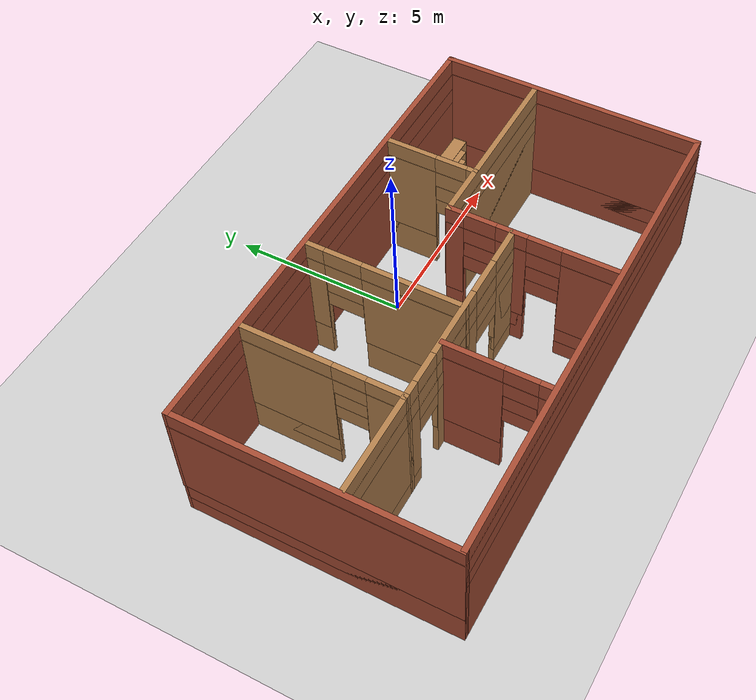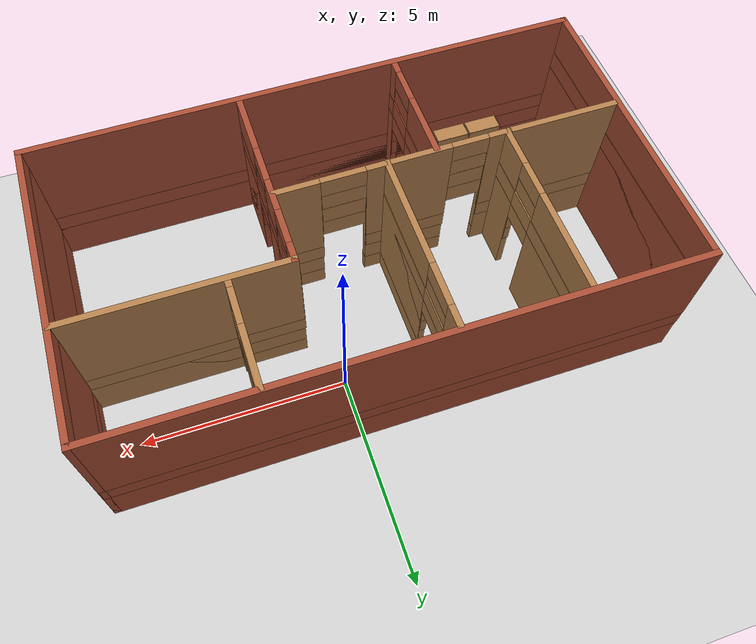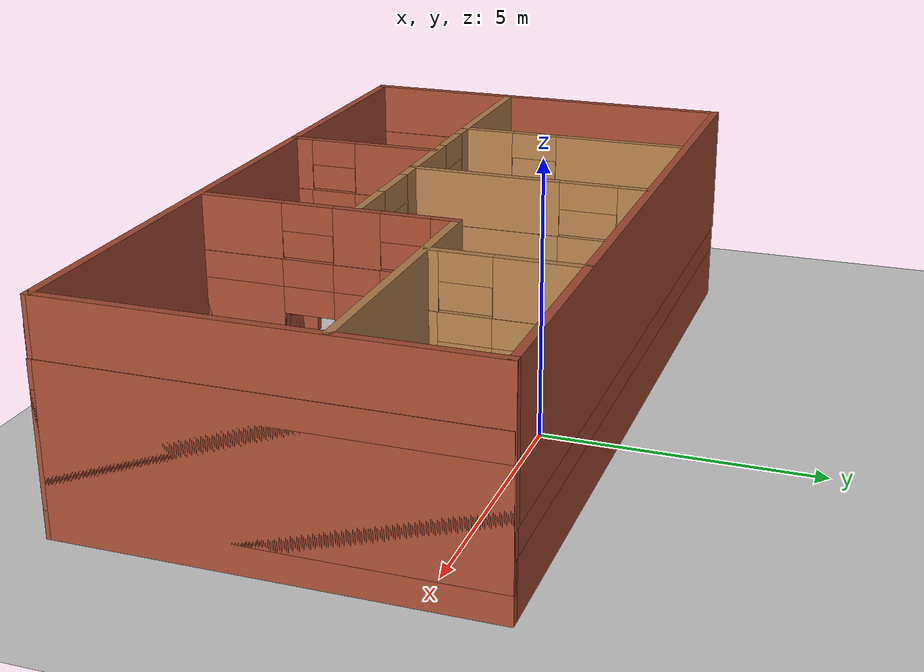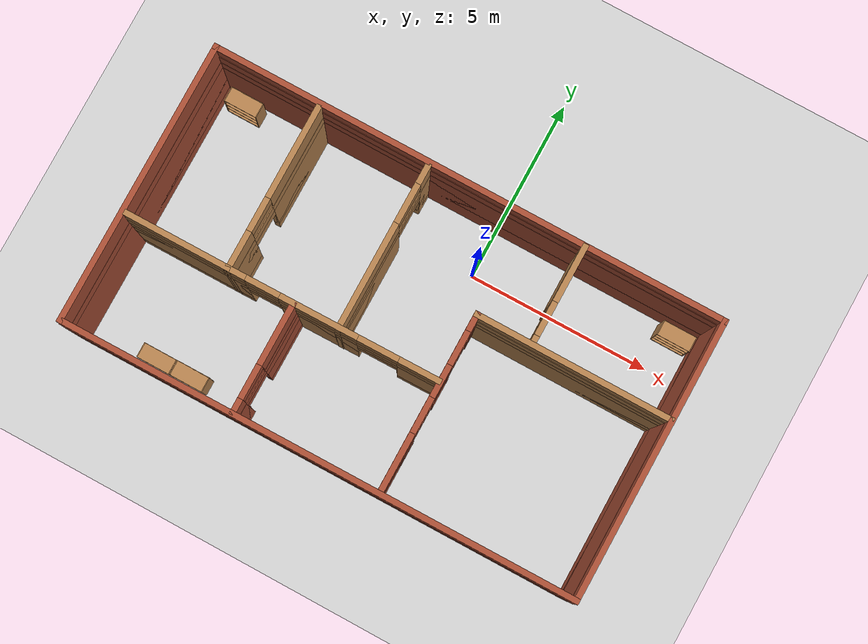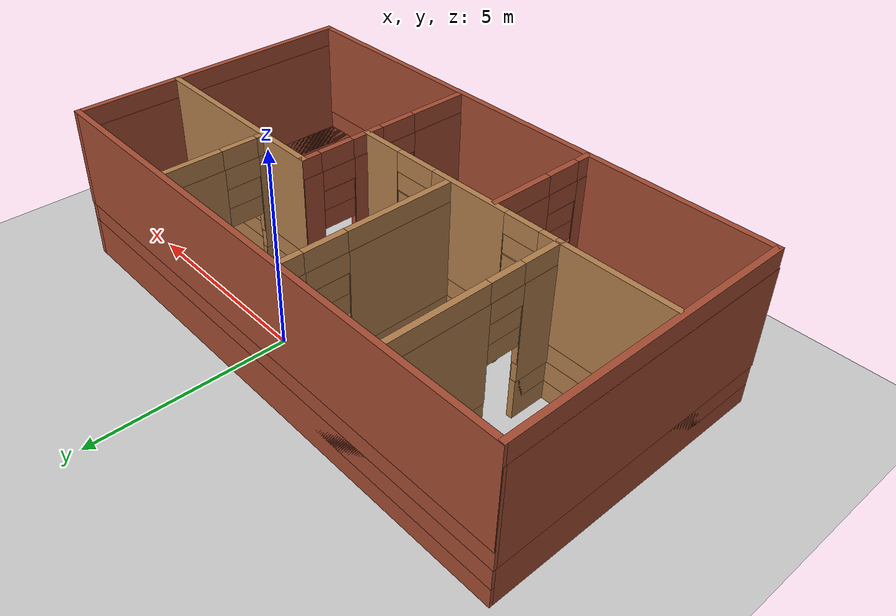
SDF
<sdf version="1.7">
 <world name="default">
  <model name="ground_plane">
   <static>1</static>
   <link name="link">
    <collision name="collision">
     <geometry><plane><normal>0 0 1</normal><size>100 100</size></plane></geometry>
     <surface><friction><ode><mu>100</mu><mu2>50</mu2></ode></friction></surface>
    </collision>
    <visual name="visual">
     <cast_shadows>0</cast_shadows>
     <geometry><plane><normal>0 0 1</normal><size>100 100</size></plane></geometry>
     <material>
      <script><uri>file://media/materials/scripts/gazebo.material</uri><name>Gazebo/Grey</name></script>
     </material>
    </visual>
   </link>
  </model>
  <gravity>0 0 -9.8</gravity>
  <magnetic_field>6e-06 2.3e-05 -4.2e-05</magnetic_field>
  <atmosphere type="adiabatic"/>
  <physics type="ode">
   <max_step_size>0.001</max_step_size>
   <real_time_factor>1</real_time_factor>
   <real_time_update_rate>1000</real_time_update_rate>
  </physics>
  <scene><ambient>0.4 0.4 0.4 1</ambient><background>0.7 0.7 0.7 1</background><shadows>1</shadows></scene>
  <spherical_coordinates>
   <surface_model>EARTH_WGS84</surface_model>
   <latitude_deg>0</latitude_deg>
   <longitude_deg>0</longitude_deg>
   <elevation>0</elevation>
   <heading_deg>0</heading_deg>
  </spherical_coordinates>
  <model name="Home">
   <pose>-1 -2.37 0 0 -0 0</pose>
   <link name="Wall_12">
    <pose>1.66056 -1.22804 0 0 -0 1.5708</pose>
    <visual name="Wall_12_Visual_0">
     <pose>-1.61056 0 1.25 0 -0 0</pose>
     <geometry><box><size>1.52888 0.15 2.5</size></box></geometry>
     <material>
      <script><uri>file://media/materials/scripts/gazebo.material</uri><name>Gazebo/Bricks</name></script>
      <ambient>1 1 1 1</ambient>
     </material>
     <meta><layer>0</layer></meta>
    </visual>
    <collision name="Wall_12_Collision_0">
     <geometry><box><size>1.52888 0.15 2.5</size></box></geometry>
     <pose>-1.61056 0 1.25 0 -0 0</pose>
    </collision>
    <visual name="Wall_12_Visual_1">
     <pose>0.530674 0 1.25 0 -0 0</pose>
     <geometry><box><size>0.861072 0.15 2.5</size></box></geometry>
     <material>
      <script><uri>file://media/materials/scripts/gazebo.material</uri><name>Gazebo/Bricks</name></script>
      <ambient>1 1 1 1</ambient>
     </material>
     <meta><layer>0</layer></meta>
    </visual>
    <collision name="Wall_12_Collision_1">
     <geometry><box><size>0.861072 0.15 2.5</size></box></geometry>
     <pose>0.530674 0 1.25 0 -0 0</pose>
    </collision>
    <visual name="Wall_12_Visual_2">
     <pose>2.1181 0 1.25 0 -0 0</pose>
     <geometry><box><size>0.51379 0.15 2.5</size></box></geometry>
     <material>
      <script><uri>file://media/materials/scripts/gazebo.material</uri><name>Gazebo/Bricks</name></script>
      <ambient>1 1 1 1</ambient>
     </material>
     <meta><layer>0</layer></meta>
    </visual>
    <collision name="Wall_12_Collision_2">
     <geometry><box><size>0.51379 0.15 2.5</size></box></geometry>
     <pose>2.1181 0 1.25 0 -0 0</pose>
    </collision>
    <visual name="Wall_12_Visual_3">
     <pose>-0.372993 0 2.25 0 -0 0</pose>
     <geometry><box><size>0.946261 0.15 0.5</size></box></geometry>
     <material>
      <script><uri>file://media/materials/scripts/gazebo.material</uri><name>Gazebo/Bricks</name></script>
      <ambient>1 1 1 1</ambient>
     </material>
     <meta><layer>0</layer></meta>
    </visual>
    <collision name="Wall_12_Collision_3">
     <geometry><box><size>0.946261 0.15 0.5</size></box></geometry>
     <pose>-0.372993 0 2.25 0 -0 0</pose>
    </collision>
    <visual name="Wall_12_Visual_4">
     <pose>1.41121 0 2.25 0 -0 0</pose>
     <geometry><box><size>0.9 0.15 0.5</size></box></geometry>
     <material>
      <script><uri>file://media/materials/scripts/gazebo.material</uri><name>Gazebo/Bricks</name></script>
      <ambient>1 1 1 1</ambient>
     </material>
     <meta><layer>0</layer></meta>
    </visual>
    <collision name="Wall_12_Collision_4">
     <geometry><box><size>0.9 0.15 0.5</size></box></geometry>
     <pose>1.41121 0 2.25 0 -0 0</pose>
    </collision>
   </link>
   <link name="Wall_13">
    <collision name="Wall_13_Collision">
     <geometry><box><size>5.25 0.15 2.5</size></box></geometry>
     <pose>0 0 1.25 0 -0 0</pose>
    </collision>
    <visual name="Wall_13_Visual">
     <pose>0 0 1.25 0 -0 0</pose>
     <geometry><box><size>5.25 0.15 2.5</size></box></geometry>
     <material>
      <script><uri>file://media/materials/scripts/gazebo.material</uri><name>Gazebo/Wood</name></script>
      <ambient>1 1 1 1</ambient>
     </material>
     <meta><layer>0</layer></meta>
    </visual>
    <pose>4.21056 1.07196 0 0 -0 0</pose>
   </link>
   <link name="Wall_15">
    <pose>3.11696 2.38389 0 0 -0 1.5708</pose>
    <visual name="Wall_15_Visual_0">
     <pose>-1.22409 0 1.25 0 -0 0</pose>
     <geometry><box><size>0.301812 0.15 2.5</size></box></geometry>
     <material>
      <script><uri>file://media/materials/scripts/gazebo.material</uri><name>Gazebo/Wood</name></script>
      <ambient>1 1 1 1</ambient>
     </material>
     <meta><layer>0</layer></meta>
    </visual>
    <collision name="Wall_15_Collision_0">
     <geometry><box><size>0.301812 0.15 2.5</size></box></geometry>
     <pose>-1.22409 0 1.25 0 -0 0</pose>
    </collision>
    <visual name="Wall_15_Visual_1">
     <pose>0.600906 0 1.25 0 -0 0</pose>
     <geometry><box><size>1.54819 0.15 2.5</size></box></geometry>
     <material>
      <script><uri>file://media/materials/scripts/gazebo.material</uri><name>Gazebo/Wood</name></script>
      <ambient>1 1 1 1</ambient>
     </material>
     <meta><layer>0</layer></meta>
    </visual>
    <collision name="Wall_15_Collision_1">
     <geometry><box><size>1.54819 0.15 2.5</size></box></geometry>
     <pose>0.600906 0 1.25 0 -0 0</pose>
    </collision>
    <visual name="Wall_15_Visual_2">
     <pose>-0.623188 0 2.25 0 -0 0</pose>
     <geometry><box><size>0.9 0.15 0.5</size></box></geometry>
     <material>
      <script><uri>file://media/materials/scripts/gazebo.material</uri><name>Gazebo/Wood</name></script>
      <ambient>1 1 1 1</ambient>
     </material>
     <meta><layer>0</layer></meta>
    </visual>
    <collision name="Wall_15_Collision_2">
     <geometry><box><size>0.9 0.15 0.5</size></box></geometry>
     <pose>-0.623188 0 2.25 0 -0 0</pose>
    </collision>
   </link>
   <link name="Wall_18">
    <pose>-3.96332 1.41133 0 0 -0 -1.5708</pose>
    <visual name="Wall_18_Visual_0">
     <pose>-0.988781 0 1.25 0 -0 0</pose>
     <geometry><box><size>2.52244 0.15 2.5</size></box></geometry>
     <material>
      <script><uri>file://media/materials/scripts/gazebo.material</uri><name>Gazebo/Wood</name></script>
      <ambient>1 1 1 1</ambient>
     </material>
     <meta><layer>0</layer></meta>
    </visual>
    <collision name="Wall_18_Collision_0">
     <geometry><box><size>2.52244 0.15 2.5</size></box></geometry>
     <pose>-0.988781 0 1.25 0 -0 0</pose>
    </collision>
    <visual name="Wall_18_Visual_1">
     <pose>1.71122 0 1.25 0 -0 0</pose>
     <geometry><box><size>1.07756 0.15 2.5</size></box></geometry>
     <material>
      <script><uri>file://media/materials/scripts/gazebo.material</uri><name>Gazebo/Wood</name></script>
      <ambient>1 1 1 1</ambient>
     </material>
     <meta><layer>0</layer></meta>
    </visual>
    <collision name="Wall_18_Collision_1">
     <geometry><box><size>1.07756 0.15 2.5</size></box></geometry>
     <pose>1.71122 0 1.25 0 -0 0</pose>
    </collision>
    <visual name="Wall_18_Visual_2">
     <pose>0.722438 0 2.25 0 -0 0</pose>
     <geometry><box><size>0.9 0.15 0.5</size></box></geometry>
     <material>
      <script><uri>file://media/materials/scripts/gazebo.material</uri><name>Gazebo/Wood</name></script>
      <ambient>1 1 1 1</ambient>
     </material>
     <meta><layer>0</layer></meta>
    </visual>
    <collision name="Wall_18_Collision_2">
     <geometry><box><size>0.9 0.15 0.5</size></box></geometry>
     <pose>0.722438 0 2.25 0 -0 0</pose>
    </collision>
   </link>
   <link name="Wall_19">
    <pose>-1.18914 -0.740536 0 0 -0 0.008269</pose>
    <visual name="Wall_19_Visual_0">
     <pose>-2.59209 0 1.25 0 -0 0</pose>
     <geometry><box><size>0.560625 0.15 2.5</size></box></geometry>
     <material>
      <script><uri>file://media/materials/scripts/gazebo.material</uri><name>Gazebo/Wood</name></script>
      <ambient>1 1 1 1</ambient>
     </material>
     <meta><layer>0</layer></meta>
    </visual>
    <collision name="Wall_19_Collision_0">
     <geometry><box><size>0.560625 0.15 2.5</size></box></geometry>
     <pose>-2.59209 0 1.25 0 -0 0</pose>
    </collision>
    <visual name="Wall_19_Visual_1">
     <pose>-0.371666 0 1.25 0 -0 0</pose>
     <geometry><box><size>2.08022 0.15 2.5</size></box></geometry>
     <material>
      <script><uri>file://media/materials/scripts/gazebo.material</uri><name>Gazebo/Wood</name></script>
      <ambient>1 1 1 1</ambient>
     </material>
     <meta><layer>0</layer></meta>
    </visual>
    <collision name="Wall_19_Collision_1">
     <geometry><box><size>2.08022 0.15 2.5</size></box></geometry>
     <pose>-0.371666 0 1.25 0 -0 0</pose>
    </collision>
    <visual name="Wall_19_Visual_2">
     <pose>2.31313 0 1.25 0 -0 0</pose>
     <geometry><box><size>1.11854 0.15 2.5</size></box></geometry>
     <material>
      <script><uri>file://media/materials/scripts/gazebo.material</uri><name>Gazebo/Wood</name></script>
      <ambient>1 1 1 1</ambient>
     </material>
     <meta><layer>0</layer></meta>
    </visual>
    <collision name="Wall_19_Collision_2">
     <geometry><box><size>1.11854 0.15 2.5</size></box></geometry>
     <pose>2.31313 0 1.25 0 -0 0</pose>
    </collision>
    <visual name="Wall_19_Visual_3">
     <pose>-1.86178 0 2.25 0 -0 0</pose>
     <geometry><box><size>0.9 0.15 0.5</size></box></geometry>
     <material>
      <script><uri>file://media/materials/scripts/gazebo.material</uri><name>Gazebo/Wood</name></script>
      <ambient>1 1 1 1</ambient>
     </material>
     <meta><layer>0</layer></meta>
    </visual>
    <collision name="Wall_19_Collision_3">
     <geometry><box><size>0.9 0.15 0.5</size></box></geometry>
     <pose>-1.86178 0 2.25 0 -0 0</pose>
    </collision>
    <visual name="Wall_19_Visual_4">
     <pose>1.21116 0 2.25 0 -0 0</pose>
     <geometry><box><size>1.08542 0.15 0.5</size></box></geometry>
     <material>
      <script><uri>file://media/materials/scripts/gazebo.material</uri><name>Gazebo/Wood</name></script>
      <ambient>1 1 1 1</ambient>
     </material>
     <meta><layer>0</layer></meta>
    </visual>
    <collision name="Wall_19_Collision_4">
     <geometry><box><size>1.08542 0.15 0.5</size></box></geometry>
     <pose>1.21116 0 2.25 0 -0 0</pose>
    </collision>
   </link>
   <link name="Wall_30">
    <collision name="Wall_30_Collision">
     <geometry><box><size>2.84783 0.15 2.5</size></box></geometry>
     <pose>0 0 1.25 0 -0 0</pose>
    </collision>
    <visual name="Wall_30_Visual">
     <pose>0 0 1.25 0 -0 0</pose>
     <geometry><box><size>2.84783 0.15 2.5</size></box></geometry>
     <material>
      <script><uri>file://media/materials/scripts/gazebo.material</uri><name>Gazebo/Wood</name></script>
      <ambient>1 1 1 1</ambient>
     </material>
     <meta><layer>0</layer></meta>
    </visual>
    <pose>-5.33536 -0.766722 0 0 -0 0.002265</pose>
   </link>
   <link name="Wall_35">
    <pose>-2.22395 -2.216 0 0 -0 -1.5708</pose>
    <visual name="Wall_35_Visual_0">
     <pose>-0.661897 0 1.25 0 -0 0</pose>
     <geometry><box><size>1.67621 0.15 2.5</size></box></geometry>
     <material>
      <script><uri>file://media/materials/scripts/gazebo.material</uri><name>Gazebo/Bricks</name></script>
      <ambient>1 1 1 1</ambient>
     </material>
     <meta><layer>0</layer></meta>
    </visual>
    <collision name="Wall_35_Collision_0">
     <geometry><box><size>1.67621 0.15 2.5</size></box></geometry>
     <pose>-0.661897 0 1.25 0 -0 0</pose>
    </collision>
    <visual name="Wall_35_Visual_1">
     <pose>1.2881 0 1.25 0 -0 0</pose>
     <geometry><box><size>0.423793 0.15 2.5</size></box></geometry>
     <material>
      <script><uri>file://media/materials/scripts/gazebo.material</uri><name>Gazebo/Bricks</name></script>
      <ambient>1 1 1 1</ambient>
     </material>
     <meta><layer>0</layer></meta>
    </visual>
    <collision name="Wall_35_Collision_1">
     <geometry><box><size>0.423793 0.15 2.5</size></box></geometry>
     <pose>1.2881 0 1.25 0 -0 0</pose>
    </collision>
    <visual name="Wall_35_Visual_2">
     <pose>0.626207 0 2.25 0 -0 0</pose>
     <geometry><box><size>0.9 0.15 0.5</size></box></geometry>
     <material>
      <script><uri>file://media/materials/scripts/gazebo.material</uri><name>Gazebo/Bricks</name></script>
      <ambient>1 1 1 1</ambient>
     </material>
     <meta><layer>0</layer></meta>
    </visual>
    <collision name="Wall_35_Collision_2">
     <geometry><box><size>0.9 0.15 0.5</size></box></geometry>
     <pose>0.626207 0 2.25 0 -0 0</pose>
    </collision>
   </link>
   <link name="Wall_37">
    <pose>-1.02777 1.42469 0 0 -0 1.5708</pose>
    <visual name="Wall_37_Visual_0">
     <pose>-0.80612 0 1.25 0 -0 0</pose>
     <geometry><box><size>2.88776 0.15 2.5</size></box></geometry>
     <material>
      <script><uri>file://media/materials/scripts/gazebo.material</uri><name>Gazebo/Wood</name></script>
      <ambient>1 1 1 1</ambient>
     </material>
     <meta><layer>0</layer></meta>
    </visual>
    <collision name="Wall_37_Collision_0">
     <geometry><box><size>2.88776 0.15 2.5</size></box></geometry>
     <pose>-0.80612 0 1.25 0 -0 0</pose>
    </collision>
    <visual name="Wall_37_Visual_1">
     <pose>1.97484 0 1.25 0 -0 0</pose>
     <geometry><box><size>0.550325 0.15 2.5</size></box></geometry>
     <material>
      <script><uri>file://media/materials/scripts/gazebo.material</uri><name>Gazebo/Wood</name></script>
      <ambient>1 1 1 1</ambient>
     </material>
     <meta><layer>0</layer></meta>
    </visual>
    <collision name="Wall_37_Collision_1">
     <geometry><box><size>0.550325 0.15 2.5</size></box></geometry>
     <pose>1.97484 0 1.25 0 -0 0</pose>
    </collision>
    <visual name="Wall_37_Visual_2">
     <pose>1.16872 0 2.25 0 -0 0</pose>
     <geometry><box><size>1.06191 0.15 0.5</size></box></geometry>
     <material>
      <script><uri>file://media/materials/scripts/gazebo.material</uri><name>Gazebo/Wood</name></script>
      <ambient>1 1 1 1</ambient>
     </material>
     <meta><layer>0</layer></meta>
    </visual>
    <collision name="Wall_37_Collision_2">
     <geometry><box><size>1.06191 0.15 0.5</size></box></geometry>
     <pose>1.16872 0 2.25 0 -0 0</pose>
    </collision>
   </link>
   <link name="Wall_4">
    <collision name="Wall_4_Collision">
     <geometry><box><size>7.54823 0.15 2.5</size></box></geometry>
     <pose>0 0 1.25 0 -0 0</pose>
    </collision>
    <visual name="Wall_4_Visual">
     <pose>0 0 1.25 0 -0 0</pose>
     <geometry><box><size>7.54823 0.15 2.5</size></box></geometry>
     <material>
      <script><uri>file://media/materials/scripts/gazebo.material</uri><name>Gazebo/Bricks</name></script>
      <ambient>1 1 1 1</ambient>
     </material>
     <meta><layer>0</layer></meta>
    </visual>
    <pose>-6.80015 -0.007429 0 0 -0 1.5701</pose>
   </link>
   <link name="Wall_5">
    <collision name="Wall_5_Collision">
     <geometry><box><size>13.75 0.15 2.5</size></box></geometry>
     <pose>0 0 1.25 0 -0 0</pose>
    </collision>
    <visual name="Wall_5_Visual">
     <pose>0 0 1.25 0 -0 0</pose>
     <geometry><box><size>13.75 0.15 2.5</size></box></geometry>
     <material>
      <script><uri>file://media/materials/scripts/gazebo.material</uri><name>Gazebo/Bricks</name></script>
      <ambient>1 1 1 1</ambient>
     </material>
     <meta><layer>0</layer></meta>
    </visual>
    <pose>0.002433 3.70689 0 0 -0 0</pose>
   </link>
   <link name="Wall_6">
    <collision name="Wall_6_Collision">
     <geometry><box><size>7.5 0.15 2.5</size></box></geometry>
     <pose>0 0 1.25 0 -0 0</pose>
    </collision>
    <visual name="Wall_6_Visual">
     <pose>0 0 1.25 0 -0 0</pose>
     <geometry><box><size>7.5 0.15 2.5</size></box></geometry>
     <material>
      <script><uri>file://media/materials/scripts/gazebo.material</uri><name>Gazebo/Bricks</name></script>
      <ambient>1 1 1 1</ambient>
     </material>
     <meta><layer>0</layer></meta>
    </visual>
    <pose>6.80243 0.031891 0 0 -0 -1.5708</pose>
   </link>
   <link name="Wall_7">
    <collision name="Wall_7_Collision">
     <geometry><box><size>13.7088 0.15 2.5</size></box></geometry>
     <pose>0 0 1.25 0 -0 0</pose>
    </collision>
    <visual name="Wall_7_Visual">
     <pose>0 0 1.25 0 -0 0</pose>
     <geometry><box><size>13.7088 0.15 2.5</size></box></geometry>
     <material>
      <script><uri>file://media/materials/scripts/gazebo.material</uri><name>Gazebo/Bricks</name></script>
      <ambient>1 1 1 1</ambient>
     </material>
     <meta><layer>0</layer></meta>
    </visual>
    <pose>0.023113 -3.67482 0 0 -0 -3.13691</pose>
   </link>
   <static>1</static>
  </model>
  <model name="bookshelf">
   <static>1</static>
   <link name="link">
    <inertial><mass>1</mass></inertial>
    <collision name="back">
     <pose>0 0.005 0.6 0 -0 0</pose>
     <geometry><box><size>0.9 0.01 1.2</size></box></geometry>
    </collision>
    <visual name="visual1">
     <pose>0 0.005 0.6 0 -0 0</pose>
     <geometry><box><size>0.9 0.01 1.2</size></box></geometry>
     <material>
      <script><uri>file://media/materials/scripts/gazebo.material</uri><name>Gazebo/Wood</name></script>
     </material>
    </visual>
    <collision name="left_side">
     <pose>0.45 -0.195 0.6 0 -0 0</pose>
     <geometry><box><size>0.02 0.4 1.2</size></box></geometry>
    </collision>
    <visual name="visual2">
     <pose>0.45 -0.195 0.6 0 -0 0</pose>
     <geometry><box><size>0.02 0.4 1.2</size></box></geometry>
     <material>
      <script><uri>file://media/materials/scripts/gazebo.material</uri><name>Gazebo/Wood</name></script>
     </material>
    </visual>
    <collision name="right_side">
     <pose>-0.45 -0.195 0.6 0 -0 0</pose>
     <geometry><box><size>0.02 0.4 1.2</size></box></geometry>
    </collision>
    <visual name="visual3">
     <pose>-0.45 -0.195 0.6 0 -0 0</pose>
     <geometry><box><size>0.02 0.4 1.2</size></box></geometry>
     <material>
      <script><uri>file://media/materials/scripts/gazebo.material</uri><name>Gazebo/Wood</name></script>
     </material>
    </visual>
    <collision name="bottom">
     <pose>0 -0.195 0.03 0 -0 0</pose>
     <geometry><box><size>0.88 0.4 0.06</size></box></geometry>
    </collision>
    <visual name="visual4">
     <pose>0 -0.195 0.03 0 -0 0</pose>
     <geometry><box><size>0.88 0.4 0.06</size></box></geometry>
     <material>
      <script><uri>file://media/materials/scripts/gazebo.material</uri><name>Gazebo/Wood</name></script>
     </material>
    </visual>
    <collision name="top">
     <pose>0 -0.195 1.19 0 -0 0</pose>
     <geometry><box><size>0.88 0.4 0.02</size></box></geometry>
    </collision>
    <visual name="visual5">
     <pose>0 -0.195 1.19 0 -0 0</pose>
     <geometry><box><size>0.88 0.4 0.02</size></box></geometry>
     <material>
      <script><uri>file://media/materials/scripts/gazebo.material</uri><name>Gazebo/Wood</name></script>
     </material>
    </visual>
    <collision name="low_shelf">
     <pose>0 -0.195 0.43 0 -0 0</pose>
     <geometry><box><size>0.88 0.4 0.02</size></box></geometry>
    </collision>
    <visual name="visual6">
     <pose>0 -0.195 0.43 0 -0 0</pose>
     <geometry><box><size>0.88 0.4 0.02</size></box></geometry>
     <material>
      <script><uri>file://media/materials/scripts/gazebo.material</uri><name>Gazebo/Wood</name></script>
     </material>
    </visual>
    <collision name="high_shelf">
     <pose>0 -0.195 0.8 0 -0 0</pose>
     <geometry><box><size>0.88 0.4 0.02</size></box></geometry>
    </collision>
    <visual name="visual7">
     <pose>0 -0.195 0.8 0 -0 0</pose>
     <geometry><box><size>0.88 0.4 0.02</size></box></geometry>
     <material>
      <script><uri>file://media/materials/scripts/gazebo.material</uri><name>Gazebo/Wood</name></script>
     </material>
    </visual>
   </link>
   <pose>5.21081 1.16254 0 0 -0 0</pose>
  </model>
  <model name="bookshelf_0">
   <static>1</static>
   <link name="link">
    <inertial><mass>1</mass></inertial>
    <collision name="back">
     <pose>0 0.005 0.6 0 -0 0</pose>
     <geometry><box><size>0.9 0.01 1.2</size></box></geometry>
    </collision>
    <visual name="visual1">
     <pose>0 0.005 0.6 0 -0 0</pose>
     <geometry><box><size>0.9 0.01 1.2</size></box></geometry>
     <material>
      <script><uri>file://media/materials/scripts/gazebo.material</uri><name>Gazebo/Wood</name></script>
     </material>
    </visual>
    <collision name="left_side">
     <pose>0.45 -0.195 0.6 0 -0 0</pose>
     <geometry><box><size>0.02 0.4 1.2</size></box></geometry>
    </collision>
    <visual name="visual2">
     <pose>0.45 -0.195 0.6 0 -0 0</pose>
     <geometry><box><size>0.02 0.4 1.2</size></box></geometry>
     <material>
      <script><uri>file://media/materials/scripts/gazebo.material</uri><name>Gazebo/Wood</name></script>
     </material>
    </visual>
    <collision name="right_side">
     <pose>-0.45 -0.195 0.6 0 -0 0</pose>
     <geometry><box><size>0.02 0.4 1.2</size></box></geometry>
    </collision>
    <visual name="visual3">
     <pose>-0.45 -0.195 0.6 0 -0 0</pose>
     <geometry><box><size>0.02 0.4 1.2</size></box></geometry>
     <material>
      <script><uri>file://media/materials/scripts/gazebo.material</uri><name>Gazebo/Wood</name></script>
     </material>
    </visual>
    <collision name="bottom">
     <pose>0 -0.195 0.03 0 -0 0</pose>
     <geometry><box><size>0.88 0.4 0.06</size></box></geometry>
    </collision>
    <visual name="visual4">
     <pose>0 -0.195 0.03 0 -0 0</pose>
     <geometry><box><size>0.88 0.4 0.06</size></box></geometry>
     <material>
      <script><uri>file://media/materials/scripts/gazebo.material</uri><name>Gazebo/Wood</name></script>
     </material>
    </visual>
    <collision name="top">
     <pose>0 -0.195 1.19 0 -0 0</pose>
     <geometry><box><size>0.88 0.4 0.02</size></box></geometry>
    </collision>
    <visual name="visual5">
     <pose>0 -0.195 1.19 0 -0 0</pose>
     <geometry><box><size>0.88 0.4 0.02</size></box></geometry>
     <material>
      <script><uri>file://media/materials/scripts/gazebo.material</uri><name>Gazebo/Wood</name></script>
     </material>
    </visual>
    <collision name="low_shelf">
     <pose>0 -0.195 0.43 0 -0 0</pose>
     <geometry><box><size>0.88 0.4 0.02</size></box></geometry>
    </collision>
    <visual name="visual6">
     <pose>0 -0.195 0.43 0 -0 0</pose>
     <geometry><box><size>0.88 0.4 0.02</size></box></geometry>
     <material>
      <script><uri>file://media/materials/scripts/gazebo.material</uri><name>Gazebo/Wood</name></script>
     </material>
    </visual>
    <collision name="high_shelf">
     <pose>0 -0.195 0.8 0 -0 0</pose>
     <geometry><box><size>0.88 0.4 0.02</size></box></geometry>
    </collision>
    <visual name="visual7">
     <pose>0 -0.195 0.8 0 -0 0</pose>
     <geometry><box><size>0.88 0.4 0.02</size></box></geometry>
     <material>
      <script><uri>file://media/materials/scripts/gazebo.material</uri><name>Gazebo/Wood</name></script>
     </material>
    </visual>
   </link>
   <pose>-5.832 -5.51555 0 0 -0 0</pose>
  </model>
  <model name="bookshelf_1">
   <static>1</static>
   <link name="link">
    <inertial><mass>1</mass></inertial>
    <collision name="back">
     <pose>0 0.005 0.6 0 -0 0</pose>
     <geometry><box><size>0.9 0.01 1.2</size></box></geometry>
    </collision>
    <visual name="visual1">
     <pose>0 0.005 0.6 0 -0 0</pose>
     <geometry><box><size>0.9 0.01 1.2</size></box></geometry>
     <material>
      <script><uri>file://media/materials/scripts/gazebo.material</uri><name>Gazebo/Wood</name></script>
     </material>
    </visual>
    <collision name="left_side">
     <pose>0.45 -0.195 0.6 0 -0 0</pose>
     <geometry><box><size>0.02 0.4 1.2</size></box></geometry>
    </collision>
    <visual name="visual2">
     <pose>0.45 -0.195 0.6 0 -0 0</pose>
     <geometry><box><size>0.02 0.4 1.2</size></box></geometry>
     <material>
      <script><uri>file://media/materials/scripts/gazebo.material</uri><name>Gazebo/Wood</name></script>
     </material>
    </visual>
    <collision name="right_side">
     <pose>-0.45 -0.195 0.6 0 -0 0</pose>
     <geometry><box><size>0.02 0.4 1.2</size></box></geometry>
    </collision>
    <visual name="visual3">
     <pose>-0.45 -0.195 0.6 0 -0 0</pose>
     <geometry><box><size>0.02 0.4 1.2</size></box></geometry>
     <material>
      <script><uri>file://media/materials/scripts/gazebo.material</uri><name>Gazebo/Wood</name></script>
     </material>
    </visual>
    <collision name="bottom">
     <pose>0 -0.195 0.03 0 -0 0</pose>
     <geometry><box><size>0.88 0.4 0.06</size></box></geometry>
    </collision>
    <visual name="visual4">
     <pose>0 -0.195 0.03 0 -0 0</pose>
     <geometry><box><size>0.88 0.4 0.06</size></box></geometry>
     <material>
      <script><uri>file://media/materials/scripts/gazebo.material</uri><name>Gazebo/Wood</name></script>
     </material>
    </visual>
    <collision name="top">
     <pose>0 -0.195 1.19 0 -0 0</pose>
     <geometry><box><size>0.88 0.4 0.02</size></box></geometry>
    </collision>
    <visual name="visual5">
     <pose>0 -0.195 1.19 0 -0 0</pose>
     <geometry><box><size>0.88 0.4 0.02</size></box></geometry>
     <material>
      <script><uri>file://media/materials/scripts/gazebo.material</uri><name>Gazebo/Wood</name></script>
     </material>
    </visual>
    <collision name="low_shelf">
     <pose>0 -0.195 0.43 0 -0 0</pose>
     <geometry><box><size>0.88 0.4 0.02</size></box></geometry>
    </collision>
    <visual name="visual6">
     <pose>0 -0.195 0.43 0 -0 0</pose>
     <geometry><box><size>0.88 0.4 0.02</size></box></geometry>
     <material>
      <script><uri>file://media/materials/scripts/gazebo.material</uri><name>Gazebo/Wood</name></script>
     </material>
    </visual>
    <collision name="high_shelf">
     <pose>0 -0.195 0.8 0 -0 0</pose>
     <geometry><box><size>0.88 0.4 0.02</size></box></geometry>
    </collision>
    <visual name="visual7">
     <pose>0 -0.195 0.8 0 -0 0</pose>
     <geometry><box><size>0.88 0.4 0.02</size></box></geometry>
     <material>
      <script><uri>file://media/materials/scripts/gazebo.material</uri><name>Gazebo/Wood</name></script>
     </material>
    </visual>
   </link>
   <pose>-4.90541 -5.51116 0 0 -0 0</pose>
  </model>
  <model name="bookshelf_2">
   <static>1</static>
   <link name="link">
    <inertial><mass>1</mass></inertial>
    <collision name="back">
     <pose>0 0.005 0.6 0 -0 0</pose>
     <geometry><box><size>0.9 0.01 1.2</size></box></geometry>
    </collision>
    <visual name="visual1">
     <pose>0 0.005 0.6 0 -0 0</pose>
     <geometry><box><size>0.9 0.01 1.2</size></box></geometry>
     <material>
      <script><uri>file://media/materials/scripts/gazebo.material</uri><name>Gazebo/Wood</name></script>
     </material>
    </visual>
    <collision name="left_side">
     <pose>0.45 -0.195 0.6 0 -0 0</pose>
     <geometry><box><size>0.02 0.4 1.2</size></box></geometry>
    </collision>
    <visual name="visual2">
     <pose>0.45 -0.195 0.6 0 -0 0</pose>
     <geometry><box><size>0.02 0.4 1.2</size></box></geometry>
     <material>
      <script><uri>file://media/materials/scripts/gazebo.material</uri><name>Gazebo/Wood</name></script>
     </material>
    </visual>
    <collision name="right_side">
     <pose>-0.45 -0.195 0.6 0 -0 0</pose>
     <geometry><box><size>0.02 0.4 1.2</size></box></geometry>
    </collision>
    <visual name="visual3">
     <pose>-0.45 -0.195 0.6 0 -0 0</pose>
     <geometry><box><size>0.02 0.4 1.2</size></box></geometry>
     <material>
      <script><uri>file://media/materials/scripts/gazebo.material</uri><name>Gazebo/Wood</name></script>
     </material>
    </visual>
    <collision name="bottom">
     <pose>0 -0.195 0.03 0 -0 0</pose>
     <geometry><box><size>0.88 0.4 0.06</size></box></geometry>
    </collision>
    <visual name="visual4">
     <pose>0 -0.195 0.03 0 -0 0</pose>
     <geometry><box><size>0.88 0.4 0.06</size></box></geometry>
     <material>
      <script><uri>file://media/materials/scripts/gazebo.material</uri><name>Gazebo/Wood</name></script>
     </material>
    </visual>
    <collision name="top">
     <pose>0 -0.195 1.19 0 -0 0</pose>
     <geometry><box><size>0.88 0.4 0.02</size></box></geometry>
    </collision>
    <visual name="visual5">
     <pose>0 -0.195 1.19 0 -0 0</pose>
     <geometry><box><size>0.88 0.4 0.02</size></box></geometry>
     <material>
      <script><uri>file://media/materials/scripts/gazebo.material</uri><name>Gazebo/Wood</name></script>
     </material>
    </visual>
    <collision name="low_shelf">
     <pose>0 -0.195 0.43 0 -0 0</pose>
     <geometry><box><size>0.88 0.4 0.02</size></box></geometry>
    </collision>
    <visual name="visual6">
     <pose>0 -0.195 0.43 0 -0 0</pose>
     <geometry><box><size>0.88 0.4 0.02</size></box></geometry>
     <material>
      <script><uri>file://media/materials/scripts/gazebo.material</uri><name>Gazebo/Wood</name></script>
     </material>
    </visual>
    <collision name="high_shelf">
     <pose>0 -0.195 0.8 0 -0 0</pose>
     <geometry><box><size>0.88 0.4 0.02</size></box></geometry>
    </collision>
    <visual name="visual7">
     <pose>0 -0.195 0.8 0 -0 0</pose>
     <geometry><box><size>0.88 0.4 0.02</size></box></geometry>
     <material>
      <script><uri>file://media/materials/scripts/gazebo.material</uri><name>Gazebo/Wood</name></script>
     </material>
    </visual>
   </link>
   <pose>-7.08662 1.15963 0 0 -0 0</pose>
  </model>
  <light name="user_point_light_0" type="point">
   <pose>-5.06498 -3.15029 1 0 -0 0</pose>
   <diffuse>0.5 0.5 0.5 1</diffuse>
   <specular>0.1 0.1 0.1 1</specular>
   <attenuation>
    <range>20</range>
    <constant>0.5</constant>
    <linear>0.01</linear>
    <quadratic>0.001</quadratic>
   </attenuation>
   <cast_shadows>0</cast_shadows>
   <direction>0 0 -1</direction>
   <spot><inner_angle>0</inner_angle><outer_angle>0</outer_angle><falloff>0</falloff></spot>
  </light>
  <light name="user_point_light_1" type="point">
   <pose>0.603194 -3.07719 1 0 -0 0</pose>
   <diffuse>0.5 0.5 0.5 1</diffuse>
   <specular>0.1 0.1 0.1 1</specular>
   <attenuation>
    <range>20</range>
    <constant>0.5</constant>
    <linear>0.01</linear>
    <quadratic>0.001</quadratic>
   </attenuation>
   <cast_shadows>0</cast_shadows>
   <direction>0 0 -1</direction>
   <spot><inner_angle>0</inner_angle><outer_angle>0</outer_angle><falloff>0</falloff></spot>
  </light>
  <model name="Home_0">
   <pose>-1 -2.37 0.5 0 -0 0</pose>
   <link name="Wall_12">
    <pose>1.66056 -1.22804 0 0 -0 1.5708</pose>
    <visual name="Wall_12_Visual_0">
     <pose>-1.61056 0 1.25 0 -0 0</pose>
     <geometry><box><size>1.52888 0.15 2.5</size></box></geometry>
     <material>
      <script><uri>file://media/materials/scripts/gazebo.material</uri><name>Gazebo/Bricks</name></script>
      <ambient>1 1 1 1</ambient>
     </material>
     <meta><layer>0</layer></meta>
    </visual>
    <collision name="Wall_12_Collision_0">
     <geometry><box><size>1.52888 0.15 2.5</size></box></geometry>
     <pose>-1.61056 0 1.25 0 -0 0</pose>
    </collision>
    <visual name="Wall_12_Visual_1">
     <pose>0.530674 0 1.25 0 -0 0</pose>
     <geometry><box><size>0.861072 0.15 2.5</size></box></geometry>
     <material>
      <script><uri>file://media/materials/scripts/gazebo.material</uri><name>Gazebo/Bricks</name></script>
      <ambient>1 1 1 1</ambient>
     </material>
     <meta><layer>0</layer></meta>
    </visual>
    <collision name="Wall_12_Collision_1">
     <geometry><box><size>0.861072 0.15 2.5</size></box></geometry>
     <pose>0.530674 0 1.25 0 -0 0</pose>
    </collision>
    <visual name="Wall_12_Visual_2">
     <pose>2.1181 0 1.25 0 -0 0</pose>
     <geometry><box><size>0.51379 0.15 2.5</size></box></geometry>
     <material>
      <script><uri>file://media/materials/scripts/gazebo.material</uri><name>Gazebo/Bricks</name></script>
      <ambient>1 1 1 1</ambient>
     </material>
     <meta><layer>0</layer></meta>
    </visual>
    <collision name="Wall_12_Collision_2">
     <geometry><box><size>0.51379 0.15 2.5</size></box></geometry>
     <pose>2.1181 0 1.25 0 -0 0</pose>
    </collision>
    <visual name="Wall_12_Visual_3">
     <pose>-0.372993 0 2.25 0 -0 0</pose>
     <geometry><box><size>0.946261 0.15 0.5</size></box></geometry>
     <material>
      <script><uri>file://media/materials/scripts/gazebo.material</uri><name>Gazebo/Bricks</name></script>
      <ambient>1 1 1 1</ambient>
     </material>
     <meta><layer>0</layer></meta>
    </visual>
    <collision name="Wall_12_Collision_3">
     <geometry><box><size>0.946261 0.15 0.5</size></box></geometry>
     <pose>-0.372993 0 2.25 0 -0 0</pose>
    </collision>
    <visual name="Wall_12_Visual_4">
     <pose>1.41121 0 2.25 0 -0 0</pose>
     <geometry><box><size>0.9 0.15 0.5</size></box></geometry>
     <material>
      <script><uri>file://media/materials/scripts/gazebo.material</uri><name>Gazebo/Bricks</name></script>
      <ambient>1 1 1 1</ambient>
     </material>
     <meta><layer>0</layer></meta>
    </visual>
    <collision name="Wall_12_Collision_4">
     <geometry><box><size>0.9 0.15 0.5</size></box></geometry>
     <pose>1.41121 0 2.25 0 -0 0</pose>
    </collision>
   </link>
   <link name="Wall_13">
    <collision name="Wall_13_Collision">
     <geometry><box><size>5.25 0.15 2.5</size></box></geometry>
     <pose>0 0 1.25 0 -0 0</pose>
    </collision>
    <visual name="Wall_13_Visual">
     <pose>0 0 1.25 0 -0 0</pose>
     <geometry><box><size>5.25 0.15 2.5</size></box></geometry>
     <material>
      <script><uri>file://media/materials/scripts/gazebo.material</uri><name>Gazebo/Wood</name></script>
      <ambient>1 1 1 1</ambient>
     </material>
     <meta><layer>0</layer></meta>
    </visual>
    <pose>4.21056 1.07196 0 0 -0 0</pose>
   </link>
   <link name="Wall_15">
    <pose>3.11696 2.38389 0 0 -0 1.5708</pose>
    <visual name="Wall_15_Visual_0">
     <pose>-1.22409 0 1.25 0 -0 0</pose>
     <geometry><box><size>0.301812 0.15 2.5</size></box></geometry>
     <material>
      <script><uri>file://media/materials/scripts/gazebo.material</uri><name>Gazebo/Wood</name></script>
      <ambient>1 1 1 1</ambient>
     </material>
     <meta><layer>0</layer></meta>
    </visual>
    <collision name="Wall_15_Collision_0">
     <geometry><box><size>0.301812 0.15 2.5</size></box></geometry>
     <pose>-1.22409 0 1.25 0 -0 0</pose>
    </collision>
    <visual name="Wall_15_Visual_1">
     <pose>0.600906 0 1.25 0 -0 0</pose>
     <geometry><box><size>1.54819 0.15 2.5</size></box></geometry>
     <material>
      <script><uri>file://media/materials/scripts/gazebo.material</uri><name>Gazebo/Wood</name></script>
      <ambient>1 1 1 1</ambient>
     </material>
     <meta><layer>0</layer></meta>
    </visual>
    <collision name="Wall_15_Collision_1">
     <geometry><box><size>1.54819 0.15 2.5</size></box></geometry>
     <pose>0.600906 0 1.25 0 -0 0</pose>
    </collision>
    <visual name="Wall_15_Visual_2">
     <pose>-0.623188 0 2.25 0 -0 0</pose>
     <geometry><box><size>0.9 0.15 0.5</size></box></geometry>
     <material>
      <script><uri>file://media/materials/scripts/gazebo.material</uri><name>Gazebo/Wood</name></script>
      <ambient>1 1 1 1</ambient>
     </material>
     <meta><layer>0</layer></meta>
    </visual>
    <collision name="Wall_15_Collision_2">
     <geometry><box><size>0.9 0.15 0.5</size></box></geometry>
     <pose>-0.623188 0 2.25 0 -0 0</pose>
    </collision>
   </link>
   <link name="Wall_18">
    <pose>-3.96332 1.41133 0 0 -0 -1.5708</pose>
    <visual name="Wall_18_Visual_0">
     <pose>-0.988781 0 1.25 0 -0 0</pose>
     <geometry><box><size>2.52244 0.15 2.5</size></box></geometry>
     <material>
      <script><uri>file://media/materials/scripts/gazebo.material</uri><name>Gazebo/Wood</name></script>
      <ambient>1 1 1 1</ambient>
     </material>
     <meta><layer>0</layer></meta>
    </visual>
    <collision name="Wall_18_Collision_0">
     <geometry><box><size>2.52244 0.15 2.5</size></box></geometry>
     <pose>-0.988781 0 1.25 0 -0 0</pose>
    </collision>
    <visual name="Wall_18_Visual_1">
     <pose>1.71122 0 1.25 0 -0 0</pose>
     <geometry><box><size>1.07756 0.15 2.5</size></box></geometry>
     <material>
      <script><uri>file://media/materials/scripts/gazebo.material</uri><name>Gazebo/Wood</name></script>
      <ambient>1 1 1 1</ambient>
     </material>
     <meta><layer>0</layer></meta>
    </visual>
    <collision name="Wall_18_Collision_1">
     <geometry><box><size>1.07756 0.15 2.5</size></box></geometry>
     <pose>1.71122 0 1.25 0 -0 0</pose>
    </collision>
    <visual name="Wall_18_Visual_2">
     <pose>0.722438 0 2.25 0 -0 0</pose>
     <geometry><box><size>0.9 0.15 0.5</size></box></geometry>
     <material>
      <script><uri>file://media/materials/scripts/gazebo.material</uri><name>Gazebo/Wood</name></script>
      <ambient>1 1 1 1</ambient>
     </material>
     <meta><layer>0</layer></meta>
    </visual>
    <collision name="Wall_18_Collision_2">
     <geometry><box><size>0.9 0.15 0.5</size></box></geometry>
     <pose>0.722438 0 2.25 0 -0 0</pose>
    </collision>
   </link>
   <link name="Wall_19">
    <pose>-1.18914 -0.740536 0 0 -0 0.008269</pose>
    <visual name="Wall_19_Visual_0">
     <pose>-2.59209 0 1.25 0 -0 0</pose>
     <geometry><box><size>0.560625 0.15 2.5</size></box></geometry>
     <material>
      <script><uri>file://media/materials/scripts/gazebo.material</uri><name>Gazebo/Wood</name></script>
      <ambient>1 1 1 1</ambient>
     </material>
     <meta><layer>0</layer></meta>
    </visual>
    <collision name="Wall_19_Collision_0">
     <geometry><box><size>0.560625 0.15 2.5</size></box></geometry>
     <pose>-2.59209 0 1.25 0 -0 0</pose>
    </collision>
    <visual name="Wall_19_Visual_1">
     <pose>-0.371666 0 1.25 0 -0 0</pose>
     <geometry><box><size>2.08022 0.15 2.5</size></box></geometry>
     <material>
      <script><uri>file://media/materials/scripts/gazebo.material</uri><name>Gazebo/Wood</name></script>
      <ambient>1 1 1 1</ambient>
     </material>
     <meta><layer>0</layer></meta>
    </visual>
    <collision name="Wall_19_Collision_1">
     <geometry><box><size>2.08022 0.15 2.5</size></box></geometry>
     <pose>-0.371666 0 1.25 0 -0 0</pose>
    </collision>
    <visual name="Wall_19_Visual_2">
     <pose>2.31313 0 1.25 0 -0 0</pose>
     <geometry><box><size>1.11854 0.15 2.5</size></box></geometry>
     <material>
      <script><uri>file://media/materials/scripts/gazebo.material</uri><name>Gazebo/Wood</name></script>
      <ambient>1 1 1 1</ambient>
     </material>
     <meta><layer>0</layer></meta>
    </visual>
    <collision name="Wall_19_Collision_2">
     <geometry><box><size>1.11854 0.15 2.5</size></box></geometry>
     <pose>2.31313 0 1.25 0 -0 0</pose>
    </collision>
    <visual name="Wall_19_Visual_3">
     <pose>-1.86178 0 2.25 0 -0 0</pose>
     <geometry><box><size>0.9 0.15 0.5</size></box></geometry>
     <material>
      <script><uri>file://media/materials/scripts/gazebo.material</uri><name>Gazebo/Wood</name></script>
      <ambient>1 1 1 1</ambient>
     </material>
     <meta><layer>0</layer></meta>
    </visual>
    <collision name="Wall_19_Collision_3">
     <geometry><box><size>0.9 0.15 0.5</size></box></geometry>
     <pose>-1.86178 0 2.25 0 -0 0</pose>
    </collision>
    <visual name="Wall_19_Visual_4">
     <pose>1.21116 0 2.25 0 -0 0</pose>
     <geometry><box><size>1.08542 0.15 0.5</size></box></geometry>
     <material>
      <script><uri>file://media/materials/scripts/gazebo.material</uri><name>Gazebo/Wood</name></script>
      <ambient>1 1 1 1</ambient>
     </material>
     <meta><layer>0</layer></meta>
    </visual>
    <collision name="Wall_19_Collision_4">
     <geometry><box><size>1.08542 0.15 0.5</size></box></geometry>
     <pose>1.21116 0 2.25 0 -0 0</pose>
    </collision>
   </link>
   <link name="Wall_30">
    <collision name="Wall_30_Collision">
     <geometry><box><size>2.84783 0.15 2.5</size></box></geometry>
     <pose>0 0 1.25 0 -0 0</pose>
    </collision>
    <visual name="Wall_30_Visual">
     <pose>0 0 1.25 0 -0 0</pose>
     <geometry><box><size>2.84783 0.15 2.5</size></box></geometry>
     <material>
      <script><uri>file://media/materials/scripts/gazebo.material</uri><name>Gazebo/Wood</name></script>
      <ambient>1 1 1 1</ambient>
     </material>
     <meta><layer>0</layer></meta>
    </visual>
    <pose>-5.33536 -0.766722 0 0 -0 0.002265</pose>
   </link>
   <link name="Wall_35">
    <pose>-2.22395 -2.216 0 0 -0 -1.5708</pose>
    <visual name="Wall_35_Visual_0">
     <pose>-0.661897 0 1.25 0 -0 0</pose>
     <geometry><box><size>1.67621 0.15 2.5</size></box></geometry>
     <material>
      <script><uri>file://media/materials/scripts/gazebo.material</uri><name>Gazebo/Bricks</name></script>
      <ambient>1 1 1 1</ambient>
     </material>
     <meta><layer>0</layer></meta>
    </visual>
    <collision name="Wall_35_Collision_0">
     <geometry><box><size>1.67621 0.15 2.5</size></box></geometry>
     <pose>-0.661897 0 1.25 0 -0 0</pose>
    </collision>
    <visual name="Wall_35_Visual_1">
     <pose>1.2881 0 1.25 0 -0 0</pose>
     <geometry><box><size>0.423793 0.15 2.5</size></box></geometry>
     <material>
      <script><uri>file://media/materials/scripts/gazebo.material</uri><name>Gazebo/Bricks</name></script>
      <ambient>1 1 1 1</ambient>
     </material>
     <meta><layer>0</layer></meta>
    </visual>
    <collision name="Wall_35_Collision_1">
     <geometry><box><size>0.423793 0.15 2.5</size></box></geometry>
     <pose>1.2881 0 1.25 0 -0 0</pose>
    </collision>
    <visual name="Wall_35_Visual_2">
     <pose>0.626207 0 2.25 0 -0 0</pose>
     <geometry><box><size>0.9 0.15 0.5</size></box></geometry>
     <material>
      <script><uri>file://media/materials/scripts/gazebo.material</uri><name>Gazebo/Bricks</name></script>
      <ambient>1 1 1 1</ambient>
     </material>
     <meta><layer>0</layer></meta>
    </visual>
    <collision name="Wall_35_Collision_2">
     <geometry><box><size>0.9 0.15 0.5</size></box></geometry>
     <pose>0.626207 0 2.25 0 -0 0</pose>
    </collision>
   </link>
   <link name="Wall_37">
    <pose>-1.02777 1.42469 0 0 -0 1.5708</pose>
    <visual name="Wall_37_Visual_0">
     <pose>-0.80612 0 1.25 0 -0 0</pose>
     <geometry><box><size>2.88776 0.15 2.5</size></box></geometry>
     <material>
      <script><uri>file://media/materials/scripts/gazebo.material</uri><name>Gazebo/Wood</name></script>
      <ambient>1 1 1 1</ambient>
     </material>
     <meta><layer>0</layer></meta>
    </visual>
    <collision name="Wall_37_Collision_0">
     <geometry><box><size>2.88776 0.15 2.5</size></box></geometry>
     <pose>-0.80612 0 1.25 0 -0 0</pose>
    </collision>
    <visual name="Wall_37_Visual_1">
     <pose>1.97484 0 1.25 0 -0 0</pose>
     <geometry><box><size>0.550325 0.15 2.5</size></box></geometry>
     <material>
      <script><uri>file://media/materials/scripts/gazebo.material</uri><name>Gazebo/Wood</name></script>
      <ambient>1 1 1 1</ambient>
     </material>
     <meta><layer>0</layer></meta>
    </visual>
    <collision name="Wall_37_Collision_1">
     <geometry><box><size>0.550325 0.15 2.5</size></box></geometry>
     <pose>1.97484 0 1.25 0 -0 0</pose>
    </collision>
    <visual name="Wall_37_Visual_2">
     <pose>1.16872 0 2.25 0 -0 0</pose>
     <geometry><box><size>1.06191 0.15 0.5</size></box></geometry>
     <material>
      <script><uri>file://media/materials/scripts/gazebo.material</uri><name>Gazebo/Wood</name></script>
      <ambient>1 1 1 1</ambient>
     </material>
     <meta><layer>0</layer></meta>
    </visual>
    <collision name="Wall_37_Collision_2">
     <geometry><box><size>1.06191 0.15 0.5</size></box></geometry>
     <pose>1.16872 0 2.25 0 -0 0</pose>
    </collision>
   </link>
   <link name="Wall_4">
    <collision name="Wall_4_Collision">
     <geometry><box><size>7.54823 0.15 2.5</size></box></geometry>
     <pose>0 0 1.25 0 -0 0</pose>
    </collision>
    <visual name="Wall_4_Visual">
     <pose>0 0 1.25 0 -0 0</pose>
     <geometry><box><size>7.54823 0.15 2.5</size></box></geometry>
     <material>
      <script><uri>file://media/materials/scripts/gazebo.material</uri><name>Gazebo/Bricks</name></script>
      <ambient>1 1 1 1</ambient>
     </material>
     <meta><layer>0</layer></meta>
    </visual>
    <pose>-6.80015 -0.007429 0 0 -0 1.5701</pose>
   </link>
   <link name="Wall_5">
    <collision name="Wall_5_Collision">
     <geometry><box><size>13.75 0.15 2.5</size></box></geometry>
     <pose>0 0 1.25 0 -0 0</pose>
    </collision>
    <visual name="Wall_5_Visual">
     <pose>0 0 1.25 0 -0 0</pose>
     <geometry><box><size>13.75 0.15 2.5</size></box></geometry>
     <material>
      <script><uri>file://media/materials/scripts/gazebo.material</uri><name>Gazebo/Bricks</name></script>
      <ambient>1 1 1 1</ambient>
     </material>
     <meta><layer>0</layer></meta>
    </visual>
    <pose>0.002433 3.70689 0 0 -0 0</pose>
   </link>
   <link name="Wall_6">
    <collision name="Wall_6_Collision">
     <geometry><box><size>7.5 0.15 2.5</size></box></geometry>
     <pose>0 0 1.25 0 -0 0</pose>
    </collision>
    <visual name="Wall_6_Visual">
     <pose>0 0 1.25 0 -0 0</pose>
     <geometry><box><size>7.5 0.15 2.5</size></box></geometry>
     <material>
      <script><uri>file://media/materials/scripts/gazebo.material</uri><name>Gazebo/Bricks</name></script>
      <ambient>1 1 1 1</ambient>
     </material>
     <meta><layer>0</layer></meta>
    </visual>
    <pose>6.80243 0.031891 0 0 -0 -1.5708</pose>
   </link>
   <link name="Wall_7">
    <collision name="Wall_7_Collision">
     <geometry><box><size>13.7088 0.15 2.5</size></box></geometry>
     <pose>0 0 1.25 0 -0 0</pose>
    </collision>
    <visual name="Wall_7_Visual">
     <pose>0 0 1.25 0 -0 0</pose>
     <geometry><box><size>13.7088 0.15 2.5</size></box></geometry>
     <material>
      <script><uri>file://media/materials/scripts/gazebo.material</uri><name>Gazebo/Bricks</name></script>
      <ambient>1 1 1 1</ambient>
     </material>
     <meta><layer>0</layer></meta>
    </visual>
    <pose>0.023113 -3.67482 0 0 -0 -3.13691</pose>
   </link>
   <static>1</static>
  </model>
  <model name="Home_1">
   <pose>-1.02012 -2.36501 1.03284 0 -0 0</pose>
   <link name="Wall_12">
    <pose>1.66056 -1.22804 0 0 -0 1.5708</pose>
    <visual name="Wall_12_Visual_0">
     <pose>-1.61056 0 1.25 0 -0 0</pose>
     <geometry><box><size>1.52888 0.15 2.5</size></box></geometry>
     <material>
      <script><uri>file://media/materials/scripts/gazebo.material</uri><name>Gazebo/Bricks</name></script>
      <ambient>1 1 1 1</ambient>
     </material>
     <meta><layer>0</layer></meta>
    </visual>
    <collision name="Wall_12_Collision_0">
     <geometry><box><size>1.52888 0.15 2.5</size></box></geometry>
     <pose>-1.61056 0 1.25 0 -0 0</pose>
    </collision>
    <visual name="Wall_12_Visual_1">
     <pose>0.530674 0 1.25 0 -0 0</pose>
     <geometry><box><size>0.861072 0.15 2.5</size></box></geometry>
     <material>
      <script><uri>file://media/materials/scripts/gazebo.material</uri><name>Gazebo/Bricks</name></script>
      <ambient>1 1 1 1</ambient>
     </material>
     <meta><layer>0</layer></meta>
    </visual>
    <collision name="Wall_12_Collision_1">
     <geometry><box><size>0.861072 0.15 2.5</size></box></geometry>
     <pose>0.530674 0 1.25 0 -0 0</pose>
    </collision>
    <visual name="Wall_12_Visual_2">
     <pose>2.1181 0 1.25 0 -0 0</pose>
     <geometry><box><size>0.51379 0.15 2.5</size></box></geometry>
     <material>
      <script><uri>file://media/materials/scripts/gazebo.material</uri><name>Gazebo/Bricks</name></script>
      <ambient>1 1 1 1</ambient>
     </material>
     <meta><layer>0</layer></meta>
    </visual>
    <collision name="Wall_12_Collision_2">
     <geometry><box><size>0.51379 0.15 2.5</size></box></geometry>
     <pose>2.1181 0 1.25 0 -0 0</pose>
    </collision>
    <visual name="Wall_12_Visual_3">
     <pose>-0.372993 0 2.25 0 -0 0</pose>
     <geometry><box><size>0.946261 0.15 0.5</size></box></geometry>
     <material>
      <script><uri>file://media/materials/scripts/gazebo.material</uri><name>Gazebo/Bricks</name></script>
      <ambient>1 1 1 1</ambient>
     </material>
     <meta><layer>0</layer></meta>
    </visual>
    <collision name="Wall_12_Collision_3">
     <geometry><box><size>0.946261 0.15 0.5</size></box></geometry>
     <pose>-0.372993 0 2.25 0 -0 0</pose>
    </collision>
    <visual name="Wall_12_Visual_4">
     <pose>1.41121 0 2.25 0 -0 0</pose>
     <geometry><box><size>0.9 0.15 0.5</size></box></geometry>
     <material>
      <script><uri>file://media/materials/scripts/gazebo.material</uri><name>Gazebo/Bricks</name></script>
      <ambient>1 1 1 1</ambient>
     </material>
     <meta><layer>0</layer></meta>
    </visual>
    <collision name="Wall_12_Collision_4">
     <geometry><box><size>0.9 0.15 0.5</size></box></geometry>
     <pose>1.41121 0 2.25 0 -0 0</pose>
    </collision>
   </link>
   <link name="Wall_13">
    <collision name="Wall_13_Collision">
     <geometry><box><size>5.25 0.15 2.5</size></box></geometry>
     <pose>0 0 1.25 0 -0 0</pose>
    </collision>
    <visual name="Wall_13_Visual">
     <pose>0 0 1.25 0 -0 0</pose>
     <geometry><box><size>5.25 0.15 2.5</size></box></geometry>
     <material>
      <script><uri>file://media/materials/scripts/gazebo.material</uri><name>Gazebo/Wood</name></script>
      <ambient>1 1 1 1</ambient>
     </material>
     <meta><layer>0</layer></meta>
    </visual>
    <pose>4.21056 1.07196 0 0 -0 0</pose>
   </link>
   <link name="Wall_15">
    <pose>3.11696 2.38389 0 0 -0 1.5708</pose>
    <visual name="Wall_15_Visual_0">
     <pose>-1.22409 0 1.25 0 -0 0</pose>
     <geometry><box><size>0.301812 0.15 2.5</size></box></geometry>
     <material>
      <script><uri>file://media/materials/scripts/gazebo.material</uri><name>Gazebo/Wood</name></script>
      <ambient>1 1 1 1</ambient>
     </material>
     <meta><layer>0</layer></meta>
    </visual>
    <collision name="Wall_15_Collision_0">
     <geometry><box><size>0.301812 0.15 2.5</size></box></geometry>
     <pose>-1.22409 0 1.25 0 -0 0</pose>
    </collision>
    <visual name="Wall_15_Visual_1">
     <pose>0.600906 0 1.25 0 -0 0</pose>
     <geometry><box><size>1.54819 0.15 2.5</size></box></geometry>
     <material>
      <script><uri>file://media/materials/scripts/gazebo.material</uri><name>Gazebo/Wood</name></script>
      <ambient>1 1 1 1</ambient>
     </material>
     <meta><layer>0</layer></meta>
    </visual>
    <collision name="Wall_15_Collision_1">
     <geometry><box><size>1.54819 0.15 2.5</size></box></geometry>
     <pose>0.600906 0 1.25 0 -0 0</pose>
    </collision>
    <visual name="Wall_15_Visual_2">
     <pose>-0.623188 0 2.25 0 -0 0</pose>
     <geometry><box><size>0.9 0.15 0.5</size></box></geometry>
     <material>
      <script><uri>file://media/materials/scripts/gazebo.material</uri><name>Gazebo/Wood</name></script>
      <ambient>1 1 1 1</ambient>
     </material>
     <meta><layer>0</layer></meta>
    </visual>
    <collision name="Wall_15_Collision_2">
     <geometry><box><size>0.9 0.15 0.5</size></box></geometry>
     <pose>-0.623188 0 2.25 0 -0 0</pose>
    </collision>
   </link>
   <link name="Wall_18">
    <pose>-3.96332 1.41133 0 0 -0 -1.5708</pose>
    <visual name="Wall_18_Visual_0">
     <pose>-0.988781 0 1.25 0 -0 0</pose>
     <geometry><box><size>2.52244 0.15 2.5</size></box></geometry>
     <material>
      <script><uri>file://media/materials/scripts/gazebo.material</uri><name>Gazebo/Wood</name></script>
      <ambient>1 1 1 1</ambient>
     </material>
     <meta><layer>0</layer></meta>
    </visual>
    <collision name="Wall_18_Collision_0">
     <geometry><box><size>2.52244 0.15 2.5</size></box></geometry>
     <pose>-0.988781 0 1.25 0 -0 0</pose>
    </collision>
    <visual name="Wall_18_Visual_1">
     <pose>1.71122 0 1.25 0 -0 0</pose>
     <geometry><box><size>1.07756 0.15 2.5</size></box></geometry>
     <material>
      <script><uri>file://media/materials/scripts/gazebo.material</uri><name>Gazebo/Wood</name></script>
      <ambient>1 1 1 1</ambient>
     </material>
     <meta><layer>0</layer></meta>
    </visual>
    <collision name="Wall_18_Collision_1">
     <geometry><box><size>1.07756 0.15 2.5</size></box></geometry>
     <pose>1.71122 0 1.25 0 -0 0</pose>
    </collision>
    <visual name="Wall_18_Visual_2">
     <pose>0.722438 0 2.25 0 -0 0</pose>
     <geometry><box><size>0.9 0.15 0.5</size></box></geometry>
     <material>
      <script><uri>file://media/materials/scripts/gazebo.material</uri><name>Gazebo/Wood</name></script>
      <ambient>1 1 1 1</ambient>
     </material>
     <meta><layer>0</layer></meta>
    </visual>
    <collision name="Wall_18_Collision_2">
     <geometry><box><size>0.9 0.15 0.5</size></box></geometry>
     <pose>0.722438 0 2.25 0 -0 0</pose>
    </collision>
   </link>
   <link name="Wall_19">
    <pose>-1.18914 -0.740536 0 0 -0 0.008269</pose>
    <visual name="Wall_19_Visual_0">
     <pose>-2.59209 0 1.25 0 -0 0</pose>
     <geometry><box><size>0.560625 0.15 2.5</size></box></geometry>
     <material>
      <script><uri>file://media/materials/scripts/gazebo.material</uri><name>Gazebo/Wood</name></script>
      <ambient>1 1 1 1</ambient>
     </material>
     <meta><layer>0</layer></meta>
    </visual>
    <collision name="Wall_19_Collision_0">
     <geometry><box><size>0.560625 0.15 2.5</size></box></geometry>
     <pose>-2.59209 0 1.25 0 -0 0</pose>
    </collision>
    <visual name="Wall_19_Visual_1">
     <pose>-0.371666 0 1.25 0 -0 0</pose>
     <geometry><box><size>2.08022 0.15 2.5</size></box></geometry>
     <material>
      <script><uri>file://media/materials/scripts/gazebo.material</uri><name>Gazebo/Wood</name></script>
      <ambient>1 1 1 1</ambient>
     </material>
     <meta><layer>0</layer></meta>
    </visual>
    <collision name="Wall_19_Collision_1">
     <geometry><box><size>2.08022 0.15 2.5</size></box></geometry>
     <pose>-0.371666 0 1.25 0 -0 0</pose>
    </collision>
    <visual name="Wall_19_Visual_2">
     <pose>2.31313 0 1.25 0 -0 0</pose>
     <geometry><box><size>1.11854 0.15 2.5</size></box></geometry>
     <material>
      <script><uri>file://media/materials/scripts/gazebo.material</uri><name>Gazebo/Wood</name></script>
      <ambient>1 1 1 1</ambient>
     </material>
     <meta><layer>0</layer></meta>
    </visual>
    <collision name="Wall_19_Collision_2">
     <geometry><box><size>1.11854 0.15 2.5</size></box></geometry>
     <pose>2.31313 0 1.25 0 -0 0</pose>
    </collision>
    <visual name="Wall_19_Visual_3">
     <pose>-1.86178 0 2.25 0 -0 0</pose>
     <geometry><box><size>0.9 0.15 0.5</size></box></geometry>
     <material>
      <script><uri>file://media/materials/scripts/gazebo.material</uri><name>Gazebo/Wood</name></script>
      <ambient>1 1 1 1</ambient>
     </material>
     <meta><layer>0</layer></meta>
    </visual>
    <collision name="Wall_19_Collision_3">
     <geometry><box><size>0.9 0.15 0.5</size></box></geometry>
     <pose>-1.86178 0 2.25 0 -0 0</pose>
    </collision>
    <visual name="Wall_19_Visual_4">
     <pose>1.21116 0 2.25 0 -0 0</pose>
     <geometry><box><size>1.08542 0.15 0.5</size></box></geometry>
     <material>
      <script><uri>file://media/materials/scripts/gazebo.material</uri><name>Gazebo/Wood</name></script>
      <ambient>1 1 1 1</ambient>
     </material>
     <meta><layer>0</layer></meta>
    </visual>
    <collision name="Wall_19_Collision_4">
     <geometry><box><size>1.08542 0.15 0.5</size></box></geometry>
     <pose>1.21116 0 2.25 0 -0 0</pose>
    </collision>
   </link>
   <link name="Wall_30">
    <collision name="Wall_30_Collision">
     <geometry><box><size>2.84783 0.15 2.5</size></box></geometry>
     <pose>0 0 1.25 0 -0 0</pose>
    </collision>
    <visual name="Wall_30_Visual">
     <pose>0 0 1.25 0 -0 0</pose>
     <geometry><box><size>2.84783 0.15 2.5</size></box></geometry>
     <material>
      <script><uri>file://media/materials/scripts/gazebo.material</uri><name>Gazebo/Wood</name></script>
      <ambient>1 1 1 1</ambient>
     </material>
     <meta><layer>0</layer></meta>
    </visual>
    <pose>-5.33536 -0.766722 0 0 -0 0.002265</pose>
   </link>
   <link name="Wall_35">
    <pose>-2.22395 -2.216 0 0 -0 -1.5708</pose>
    <visual name="Wall_35_Visual_0">
     <pose>-0.661897 0 1.25 0 -0 0</pose>
     <geometry><box><size>1.67621 0.15 2.5</size></box></geometry>
     <material>
      <script><uri>file://media/materials/scripts/gazebo.material</uri><name>Gazebo/Bricks</name></script>
      <ambient>1 1 1 1</ambient>
     </material>
     <meta><layer>0</layer></meta>
    </visual>
    <collision name="Wall_35_Collision_0">
     <geometry><box><size>1.67621 0.15 2.5</size></box></geometry>
     <pose>-0.661897 0 1.25 0 -0 0</pose>
    </collision>
    <visual name="Wall_35_Visual_1">
     <pose>1.2881 0 1.25 0 -0 0</pose>
     <geometry><box><size>0.423793 0.15 2.5</size></box></geometry>
     <material>
      <script><uri>file://media/materials/scripts/gazebo.material</uri><name>Gazebo/Bricks</name></script>
      <ambient>1 1 1 1</ambient>
     </material>
     <meta><layer>0</layer></meta>
    </visual>
    <collision name="Wall_35_Collision_1">
     <geometry><box><size>0.423793 0.15 2.5</size></box></geometry>
     <pose>1.2881 0 1.25 0 -0 0</pose>
    </collision>
    <visual name="Wall_35_Visual_2">
     <pose>0.626207 0 2.25 0 -0 0</pose>
     <geometry><box><size>0.9 0.15 0.5</size></box></geometry>
     <material>
      <script><uri>file://media/materials/scripts/gazebo.material</uri><name>Gazebo/Bricks</name></script>
      <ambient>1 1 1 1</ambient>
     </material>
     <meta><layer>0</layer></meta>
    </visual>
    <collision name="Wall_35_Collision_2">
     <geometry><box><size>0.9 0.15 0.5</size></box></geometry>
     <pose>0.626207 0 2.25 0 -0 0</pose>
    </collision>
   </link>
   <link name="Wall_37">
    <pose>-1.02777 1.42469 0 0 -0 1.5708</pose>
    <visual name="Wall_37_Visual_0">
     <pose>-0.80612 0 1.25 0 -0 0</pose>
     <geometry><box><size>2.88776 0.15 2.5</size></box></geometry>
     <material>
      <script><uri>file://media/materials/scripts/gazebo.material</uri><name>Gazebo/Wood</name></script>
      <ambient>1 1 1 1</ambient>
     </material>
     <meta><layer>0</layer></meta>
    </visual>
    <collision name="Wall_37_Collision_0">
     <geometry><box><size>2.88776 0.15 2.5</size></box></geometry>
     <pose>-0.80612 0 1.25 0 -0 0</pose>
    </collision>
    <visual name="Wall_37_Visual_1">
     <pose>1.97484 0 1.25 0 -0 0</pose>
     <geometry><box><size>0.550325 0.15 2.5</size></box></geometry>
     <material>
      <script><uri>file://media/materials/scripts/gazebo.material</uri><name>Gazebo/Wood</name></script>
      <ambient>1 1 1 1</ambient>
     </material>
     <meta><layer>0</layer></meta>
    </visual>
    <collision name="Wall_37_Collision_1">
     <geometry><box><size>0.550325 0.15 2.5</size></box></geometry>
     <pose>1.97484 0 1.25 0 -0 0</pose>
    </collision>
    <visual name="Wall_37_Visual_2">
     <pose>1.16872 0 2.25 0 -0 0</pose>
     <geometry><box><size>1.06191 0.15 0.5</size></box></geometry>
     <material>
      <script><uri>file://media/materials/scripts/gazebo.material</uri><name>Gazebo/Wood</name></script>
      <ambient>1 1 1 1</ambient>
     </material>
     <meta><layer>0</layer></meta>
    </visual>
    <collision name="Wall_37_Collision_2">
     <geometry><box><size>1.06191 0.15 0.5</size></box></geometry>
     <pose>1.16872 0 2.25 0 -0 0</pose>
    </collision>
   </link>
   <link name="Wall_4">
    <collision name="Wall_4_Collision">
     <geometry><box><size>7.54823 0.15 2.5</size></box></geometry>
     <pose>0 0 1.25 0 -0 0</pose>
    </collision>
    <visual name="Wall_4_Visual">
     <pose>0 0 1.25 0 -0 0</pose>
     <geometry><box><size>7.54823 0.15 2.5</size></box></geometry>
     <material>
      <script><uri>file://media/materials/scripts/gazebo.material</uri><name>Gazebo/Bricks</name></script>
      <ambient>1 1 1 1</ambient>
     </material>
     <meta><layer>0</layer></meta>
    </visual>
    <pose>-6.80015 -0.007429 0 0 -0 1.5701</pose>
   </link>
   <link name="Wall_5">
    <collision name="Wall_5_Collision">
     <geometry><box><size>13.75 0.15 2.5</size></box></geometry>
     <pose>0 0 1.25 0 -0 0</pose>
    </collision>
    <visual name="Wall_5_Visual">
     <pose>0 0 1.25 0 -0 0</pose>
     <geometry><box><size>13.75 0.15 2.5</size></box></geometry>
     <material>
      <script><uri>file://media/materials/scripts/gazebo.material</uri><name>Gazebo/Bricks</name></script>
      <ambient>1 1 1 1</ambient>
     </material>
     <meta><layer>0</layer></meta>
    </visual>
    <pose>0.002433 3.70689 0 0 -0 0</pose>
   </link>
   <link name="Wall_6">
    <collision name="Wall_6_Collision">
     <geometry><box><size>7.5 0.15 2.5</size></box></geometry>
     <pose>0 0 1.25 0 -0 0</pose>
    </collision>
    <visual name="Wall_6_Visual">
     <pose>0 0 1.25 0 -0 0</pose>
     <geometry><box><size>7.5 0.15 2.5</size></box></geometry>
     <material>
      <script><uri>file://media/materials/scripts/gazebo.material</uri><name>Gazebo/Bricks</name></script>
      <ambient>1 1 1 1</ambient>
     </material>
     <meta><layer>0</layer></meta>
    </visual>
    <pose>6.80243 0.031891 0 0 -0 -1.5708</pose>
   </link>
   <link name="Wall_7">
    <collision name="Wall_7_Collision">
     <geometry><box><size>13.7088 0.15 2.5</size></box></geometry>
     <pose>0 0 1.25 0 -0 0</pose>
    </collision>
    <visual name="Wall_7_Visual">
     <pose>0 0 1.25 0 -0 0</pose>
     <geometry><box><size>13.7088 0.15 2.5</size></box></geometry>
     <material>
      <script><uri>file://media/materials/scripts/gazebo.material</uri><name>Gazebo/Bricks</name></script>
      <ambient>1 1 1 1</ambient>
     </material>
     <meta><layer>0</layer></meta>
    </visual>
    <pose>0.023113 -3.67482 0 0 -0 -3.13691</pose>
   </link>
   <static>1</static>
  </model>
  <model name="Home_2">
   <pose>-1.00981 -2.35084 1.50928 0 -0 0</pose>
   <link name="Wall_12">
    <pose>1.66056 -1.22804 0 0 -0 1.5708</pose>
    <visual name="Wall_12_Visual_0">
     <pose>-1.61056 0 1.25 0 -0 0</pose>
     <geometry><box><size>1.52888 0.15 2.5</size></box></geometry>
     <material>
      <script><uri>file://media/materials/scripts/gazebo.material</uri><name>Gazebo/Bricks</name></script>
      <ambient>1 1 1 1</ambient>
     </material>
     <meta><layer>0</layer></meta>
    </visual>
    <collision name="Wall_12_Collision_0">
     <geometry><box><size>1.52888 0.15 2.5</size></box></geometry>
     <pose>-1.61056 0 1.25 0 -0 0</pose>
    </collision>
    <visual name="Wall_12_Visual_1">
     <pose>0.530674 0 1.25 0 -0 0</pose>
     <geometry><box><size>0.861072 0.15 2.5</size></box></geometry>
     <material>
      <script><uri>file://media/materials/scripts/gazebo.material</uri><name>Gazebo/Bricks</name></script>
      <ambient>1 1 1 1</ambient>
     </material>
     <meta><layer>0</layer></meta>
    </visual>
    <collision name="Wall_12_Collision_1">
     <geometry><box><size>0.861072 0.15 2.5</size></box></geometry>
     <pose>0.530674 0 1.25 0 -0 0</pose>
    </collision>
    <visual name="Wall_12_Visual_2">
     <pose>2.1181 0 1.25 0 -0 0</pose>
     <geometry><box><size>0.51379 0.15 2.5</size></box></geometry>
     <material>
      <script><uri>file://media/materials/scripts/gazebo.material</uri><name>Gazebo/Bricks</name></script>
      <ambient>1 1 1 1</ambient>
     </material>
     <meta><layer>0</layer></meta>
    </visual>
    <collision name="Wall_12_Collision_2">
     <geometry><box><size>0.51379 0.15 2.5</size></box></geometry>
     <pose>2.1181 0 1.25 0 -0 0</pose>
    </collision>
    <visual name="Wall_12_Visual_3">
     <pose>-0.372993 0 2.25 0 -0 0</pose>
     <geometry><box><size>0.946261 0.15 0.5</size></box></geometry>
     <material>
      <script><uri>file://media/materials/scripts/gazebo.material</uri><name>Gazebo/Bricks</name></script>
      <ambient>1 1 1 1</ambient>
     </material>
     <meta><layer>0</layer></meta>
    </visual>
    <collision name="Wall_12_Collision_3">
     <geometry><box><size>0.946261 0.15 0.5</size></box></geometry>
     <pose>-0.372993 0 2.25 0 -0 0</pose>
    </collision>
    <visual name="Wall_12_Visual_4">
     <pose>1.41121 0 2.25 0 -0 0</pose>
     <geometry><box><size>0.9 0.15 0.5</size></box></geometry>
     <material>
      <script><uri>file://media/materials/scripts/gazebo.material</uri><name>Gazebo/Bricks</name></script>
      <ambient>1 1 1 1</ambient>
     </material>
     <meta><layer>0</layer></meta>
    </visual>
    <collision name="Wall_12_Collision_4">
     <geometry><box><size>0.9 0.15 0.5</size></box></geometry>
     <pose>1.41121 0 2.25 0 -0 0</pose>
    </collision>
   </link>
   <link name="Wall_13">
    <collision name="Wall_13_Collision">
     <geometry><box><size>5.25 0.15 2.5</size></box></geometry>
     <pose>0 0 1.25 0 -0 0</pose>
    </collision>
    <visual name="Wall_13_Visual">
     <pose>0 0 1.25 0 -0 0</pose>
     <geometry><box><size>5.25 0.15 2.5</size></box></geometry>
     <material>
      <script><uri>file://media/materials/scripts/gazebo.material</uri><name>Gazebo/Wood</name></script>
      <ambient>1 1 1 1</ambient>
     </material>
     <meta><layer>0</layer></meta>
    </visual>
    <pose>4.21056 1.07196 0 0 -0 0</pose>
   </link>
   <link name="Wall_15">
    <pose>3.11696 2.38389 0 0 -0 1.5708</pose>
    <visual name="Wall_15_Visual_0">
     <pose>-1.22409 0 1.25 0 -0 0</pose>
     <geometry><box><size>0.301812 0.15 2.5</size></box></geometry>
     <material>
      <script><uri>file://media/materials/scripts/gazebo.material</uri><name>Gazebo/Wood</name></script>
      <ambient>1 1 1 1</ambient>
     </material>
     <meta><layer>0</layer></meta>
    </visual>
    <collision name="Wall_15_Collision_0">
     <geometry><box><size>0.301812 0.15 2.5</size></box></geometry>
     <pose>-1.22409 0 1.25 0 -0 0</pose>
    </collision>
    <visual name="Wall_15_Visual_1">
     <pose>0.600906 0 1.25 0 -0 0</pose>
     <geometry><box><size>1.54819 0.15 2.5</size></box></geometry>
     <material>
      <script><uri>file://media/materials/scripts/gazebo.material</uri><name>Gazebo/Wood</name></script>
      <ambient>1 1 1 1</ambient>
     </material>
     <meta><layer>0</layer></meta>
    </visual>
    <collision name="Wall_15_Collision_1">
     <geometry><box><size>1.54819 0.15 2.5</size></box></geometry>
     <pose>0.600906 0 1.25 0 -0 0</pose>
    </collision>
    <visual name="Wall_15_Visual_2">
     <pose>-0.623188 0 2.25 0 -0 0</pose>
     <geometry><box><size>0.9 0.15 0.5</size></box></geometry>
     <material>
      <script><uri>file://media/materials/scripts/gazebo.material</uri><name>Gazebo/Wood</name></script>
      <ambient>1 1 1 1</ambient>
     </material>
     <meta><layer>0</layer></meta>
    </visual>
    <collision name="Wall_15_Collision_2">
     <geometry><box><size>0.9 0.15 0.5</size></box></geometry>
     <pose>-0.623188 0 2.25 0 -0 0</pose>
    </collision>
   </link>
   <link name="Wall_18">
    <pose>-3.96332 1.41133 0 0 -0 -1.5708</pose>
    <visual name="Wall_18_Visual_0">
     <pose>-0.988781 0 1.25 0 -0 0</pose>
     <geometry><box><size>2.52244 0.15 2.5</size></box></geometry>
     <material>
      <script><uri>file://media/materials/scripts/gazebo.material</uri><name>Gazebo/Wood</name></script>
      <ambient>1 1 1 1</ambient>
     </material>
     <meta><layer>0</layer></meta>
    </visual>
    <collision name="Wall_18_Collision_0">
     <geometry><box><size>2.52244 0.15 2.5</size></box></geometry>
     <pose>-0.988781 0 1.25 0 -0 0</pose>
    </collision>
    <visual name="Wall_18_Visual_1">
     <pose>1.71122 0 1.25 0 -0 0</pose>
     <geometry><box><size>1.07756 0.15 2.5</size></box></geometry>
     <material>
      <script><uri>file://media/materials/scripts/gazebo.material</uri><name>Gazebo/Wood</name></script>
      <ambient>1 1 1 1</ambient>
     </material>
     <meta><layer>0</layer></meta>
    </visual>
    <collision name="Wall_18_Collision_1">
     <geometry><box><size>1.07756 0.15 2.5</size></box></geometry>
     <pose>1.71122 0 1.25 0 -0 0</pose>
    </collision>
    <visual name="Wall_18_Visual_2">
     <pose>0.722438 0 2.25 0 -0 0</pose>
     <geometry><box><size>0.9 0.15 0.5</size></box></geometry>
     <material>
      <script><uri>file://media/materials/scripts/gazebo.material</uri><name>Gazebo/Wood</name></script>
      <ambient>1 1 1 1</ambient>
     </material>
     <meta><layer>0</layer></meta>
    </visual>
    <collision name="Wall_18_Collision_2">
     <geometry><box><size>0.9 0.15 0.5</size></box></geometry>
     <pose>0.722438 0 2.25 0 -0 0</pose>
    </collision>
   </link>
   <link name="Wall_19">
    <pose>-1.18914 -0.740536 0 0 -0 0.008269</pose>
    <visual name="Wall_19_Visual_0">
     <pose>-2.59209 0 1.25 0 -0 0</pose>
     <geometry><box><size>0.560625 0.15 2.5</size></box></geometry>
     <material>
      <script><uri>file://media/materials/scripts/gazebo.material</uri><name>Gazebo/Wood</name></script>
      <ambient>1 1 1 1</ambient>
     </material>
     <meta><layer>0</layer></meta>
    </visual>
    <collision name="Wall_19_Collision_0">
     <geometry><box><size>0.560625 0.15 2.5</size></box></geometry>
     <pose>-2.59209 0 1.25 0 -0 0</pose>
    </collision>
    <visual name="Wall_19_Visual_1">
     <pose>-0.371666 0 1.25 0 -0 0</pose>
     <geometry><box><size>2.08022 0.15 2.5</size></box></geometry>
     <material>
      <script><uri>file://media/materials/scripts/gazebo.material</uri><name>Gazebo/Wood</name></script>
      <ambient>1 1 1 1</ambient>
     </material>
     <meta><layer>0</layer></meta>
    </visual>
    <collision name="Wall_19_Collision_1">
     <geometry><box><size>2.08022 0.15 2.5</size></box></geometry>
     <pose>-0.371666 0 1.25 0 -0 0</pose>
    </collision>
    <visual name="Wall_19_Visual_2">
     <pose>2.31313 0 1.25 0 -0 0</pose>
     <geometry><box><size>1.11854 0.15 2.5</size></box></geometry>
     <material>
      <script><uri>file://media/materials/scripts/gazebo.material</uri><name>Gazebo/Wood</name></script>
      <ambient>1 1 1 1</ambient>
     </material>
     <meta><layer>0</layer></meta>
    </visual>
    <collision name="Wall_19_Collision_2">
     <geometry><box><size>1.11854 0.15 2.5</size></box></geometry>
     <pose>2.31313 0 1.25 0 -0 0</pose>
    </collision>
    <visual name="Wall_19_Visual_3">
     <pose>-1.86178 0 2.25 0 -0 0</pose>
     <geometry><box><size>0.9 0.15 0.5</size></box></geometry>
     <material>
      <script><uri>file://media/materials/scripts/gazebo.material</uri><name>Gazebo/Wood</name></script>
      <ambient>1 1 1 1</ambient>
     </material>
     <meta><layer>0</layer></meta>
    </visual>
    <collision name="Wall_19_Collision_3">
     <geometry><box><size>0.9 0.15 0.5</size></box></geometry>
     <pose>-1.86178 0 2.25 0 -0 0</pose>
    </collision>
    <visual name="Wall_19_Visual_4">
     <pose>1.21116 0 2.25 0 -0 0</pose>
     <geometry><box><size>1.08542 0.15 0.5</size></box></geometry>
     <material>
      <script><uri>file://media/materials/scripts/gazebo.material</uri><name>Gazebo/Wood</name></script>
      <ambient>1 1 1 1</ambient>
     </material>
     <meta><layer>0</layer></meta>
    </visual>
    <collision name="Wall_19_Collision_4">
     <geometry><box><size>1.08542 0.15 0.5</size></box></geometry>
     <pose>1.21116 0 2.25 0 -0 0</pose>
    </collision>
   </link>
   <link name="Wall_30">
    <collision name="Wall_30_Collision">
     <geometry><box><size>2.84783 0.15 2.5</size></box></geometry>
     <pose>0 0 1.25 0 -0 0</pose>
    </collision>
    <visual name="Wall_30_Visual">
     <pose>0 0 1.25 0 -0 0</pose>
     <geometry><box><size>2.84783 0.15 2.5</size></box></geometry>
     <material>
      <script><uri>file://media/materials/scripts/gazebo.material</uri><name>Gazebo/Wood</name></script>
      <ambient>1 1 1 1</ambient>
     </material>
     <meta><layer>0</layer></meta>
    </visual>
    <pose>-5.33536 -0.766722 0 0 -0 0.002265</pose>
   </link>
   <link name="Wall_35">
    <pose>-2.22395 -2.216 0 0 -0 -1.5708</pose>
    <visual name="Wall_35_Visual_0">
     <pose>-0.661897 0 1.25 0 -0 0</pose>
     <geometry><box><size>1.67621 0.15 2.5</size></box></geometry>
     <material>
      <script><uri>file://media/materials/scripts/gazebo.material</uri><name>Gazebo/Bricks</name></script>
      <ambient>1 1 1 1</ambient>
     </material>
     <meta><layer>0</layer></meta>
    </visual>
    <collision name="Wall_35_Collision_0">
     <geometry><box><size>1.67621 0.15 2.5</size></box></geometry>
     <pose>-0.661897 0 1.25 0 -0 0</pose>
    </collision>
    <visual name="Wall_35_Visual_1">
     <pose>1.2881 0 1.25 0 -0 0</pose>
     <geometry><box><size>0.423793 0.15 2.5</size></box></geometry>
     <material>
      <script><uri>file://media/materials/scripts/gazebo.material</uri><name>Gazebo/Bricks</name></script>
      <ambient>1 1 1 1</ambient>
     </material>
     <meta><layer>0</layer></meta>
    </visual>
    <collision name="Wall_35_Collision_1">
     <geometry><box><size>0.423793 0.15 2.5</size></box></geometry>
     <pose>1.2881 0 1.25 0 -0 0</pose>
    </collision>
    <visual name="Wall_35_Visual_2">
     <pose>0.626207 0 2.25 0 -0 0</pose>
     <geometry><box><size>0.9 0.15 0.5</size></box></geometry>
     <material>
      <script><uri>file://media/materials/scripts/gazebo.material</uri><name>Gazebo/Bricks</name></script>
      <ambient>1 1 1 1</ambient>
     </material>
     <meta><layer>0</layer></meta>
    </visual>
    <collision name="Wall_35_Collision_2">
     <geometry><box><size>0.9 0.15 0.5</size></box></geometry>
     <pose>0.626207 0 2.25 0 -0 0</pose>
    </collision>
   </link>
   <link name="Wall_37">
    <pose>-1.02777 1.42469 0 0 -0 1.5708</pose>
    <visual name="Wall_37_Visual_0">
     <pose>-0.80612 0 1.25 0 -0 0</pose>
     <geometry><box><size>2.88776 0.15 2.5</size></box></geometry>
     <material>
      <script><uri>file://media/materials/scripts/gazebo.material</uri><name>Gazebo/Wood</name></script>
      <ambient>1 1 1 1</ambient>
     </material>
     <meta><layer>0</layer></meta>
    </visual>
    <collision name="Wall_37_Collision_0">
     <geometry><box><size>2.88776 0.15 2.5</size></box></geometry>
     <pose>-0.80612 0 1.25 0 -0 0</pose>
    </collision>
    <visual name="Wall_37_Visual_1">
     <pose>1.97484 0 1.25 0 -0 0</pose>
     <geometry><box><size>0.550325 0.15 2.5</size></box></geometry>
     <material>
      <script><uri>file://media/materials/scripts/gazebo.material</uri><name>Gazebo/Wood</name></script>
      <ambient>1 1 1 1</ambient>
     </material>
     <meta><layer>0</layer></meta>
    </visual>
    <collision name="Wall_37_Collision_1">
     <geometry><box><size>0.550325 0.15 2.5</size></box></geometry>
     <pose>1.97484 0 1.25 0 -0 0</pose>
    </collision>
    <visual name="Wall_37_Visual_2">
     <pose>1.16872 0 2.25 0 -0 0</pose>
     <geometry><box><size>1.06191 0.15 0.5</size></box></geometry>
     <material>
      <script><uri>file://media/materials/scripts/gazebo.material</uri><name>Gazebo/Wood</name></script>
      <ambient>1 1 1 1</ambient>
     </material>
     <meta><layer>0</layer></meta>
    </visual>
    <collision name="Wall_37_Collision_2">
     <geometry><box><size>1.06191 0.15 0.5</size></box></geometry>
     <pose>1.16872 0 2.25 0 -0 0</pose>
    </collision>
   </link>
   <link name="Wall_4">
    <collision name="Wall_4_Collision">
     <geometry><box><size>7.54823 0.15 2.5</size></box></geometry>
     <pose>0 0 1.25 0 -0 0</pose>
    </collision>
    <visual name="Wall_4_Visual">
     <pose>0 0 1.25 0 -0 0</pose>
     <geometry><box><size>7.54823 0.15 2.5</size></box></geometry>
     <material>
      <script><uri>file://media/materials/scripts/gazebo.material</uri><name>Gazebo/Bricks</name></script>
      <ambient>1 1 1 1</ambient>
     </material>
     <meta><layer>0</layer></meta>
    </visual>
    <pose>-6.80015 -0.007429 0 0 -0 1.5701</pose>
   </link>
   <link name="Wall_5">
    <collision name="Wall_5_Collision">
     <geometry><box><size>13.75 0.15 2.5</size></box></geometry>
     <pose>0 0 1.25 0 -0 0</pose>
    </collision>
    <visual name="Wall_5_Visual">
     <pose>0 0 1.25 0 -0 0</pose>
     <geometry><box><size>13.75 0.15 2.5</size></box></geometry>
     <material>
      <script><uri>file://media/materials/scripts/gazebo.material</uri><name>Gazebo/Bricks</name></script>
      <ambient>1 1 1 1</ambient>
     </material>
     <meta><layer>0</layer></meta>
    </visual>
    <pose>0.002433 3.70689 0 0 -0 0</pose>
   </link>
   <link name="Wall_6">
    <collision name="Wall_6_Collision">
     <geometry><box><size>7.5 0.15 2.5</size></box></geometry>
     <pose>0 0 1.25 0 -0 0</pose>
    </collision>
    <visual name="Wall_6_Visual">
     <pose>0 0 1.25 0 -0 0</pose>
     <geometry><box><size>7.5 0.15 2.5</size></box></geometry>
     <material>
      <script><uri>file://media/materials/scripts/gazebo.material</uri><name>Gazebo/Bricks</name></script>
      <ambient>1 1 1 1</ambient>
     </material>
     <meta><layer>0</layer></meta>
    </visual>
    <pose>6.80243 0.031891 0 0 -0 -1.5708</pose>
   </link>
   <link name="Wall_7">
    <collision name="Wall_7_Collision">
     <geometry><box><size>13.7088 0.15 2.5</size></box></geometry>
     <pose>0 0 1.25 0 -0 0</pose>
    </collision>
    <visual name="Wall_7_Visual">
     <pose>0 0 1.25 0 -0 0</pose>
     <geometry><box><size>13.7088 0.15 2.5</size></box></geometry>
     <material>
      <script><uri>file://media/materials/scripts/gazebo.material</uri><name>Gazebo/Bricks</name></script>
      <ambient>1 1 1 1</ambient>
     </material>
     <meta><layer>0</layer></meta>
    </visual>
    <pose>0.023113 -3.67482 0 0 -0 -3.13691</pose>
   </link>
   <static>1</static>
  </model>
 </world>
</sdf>
